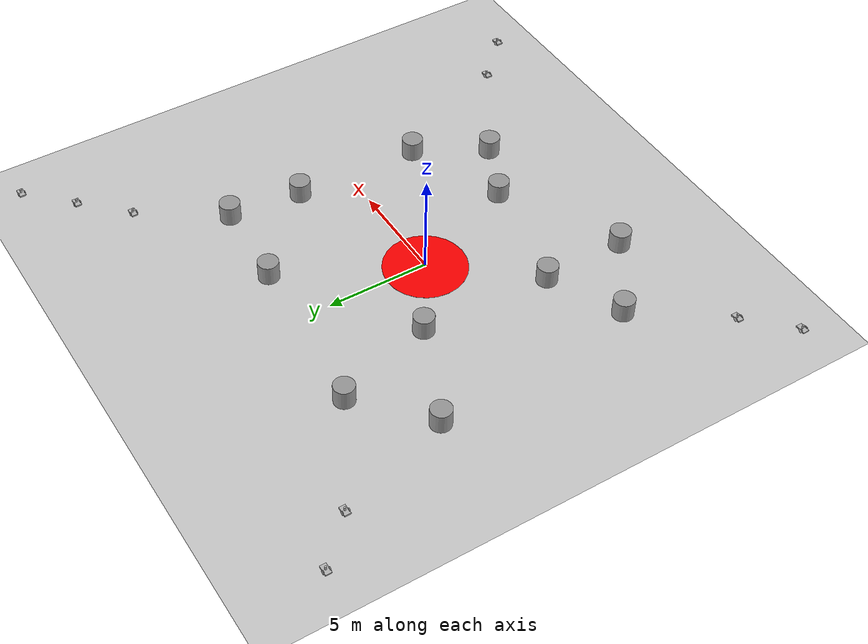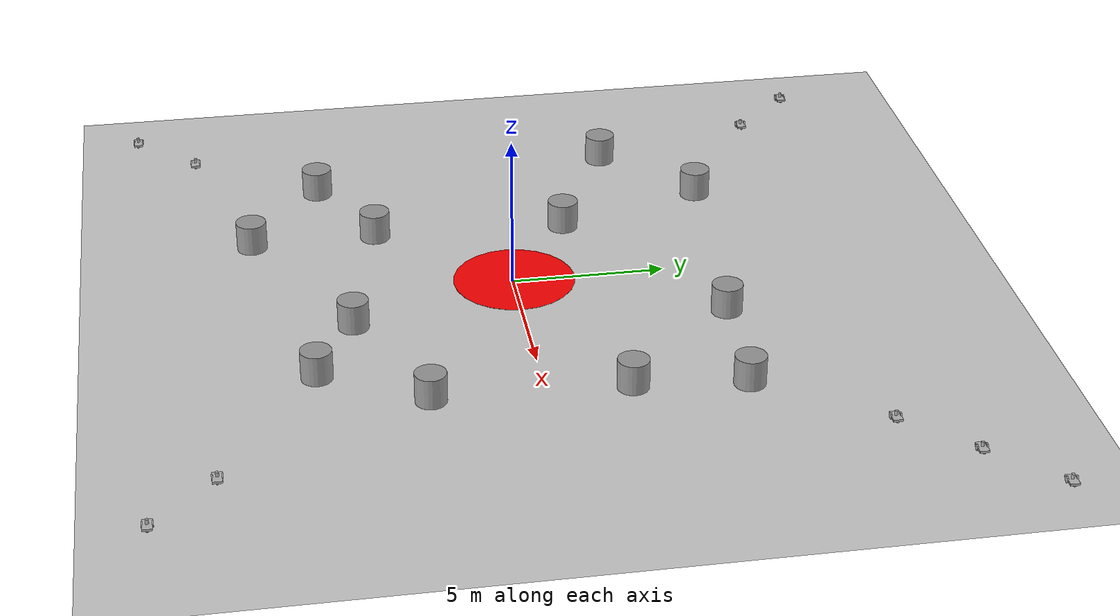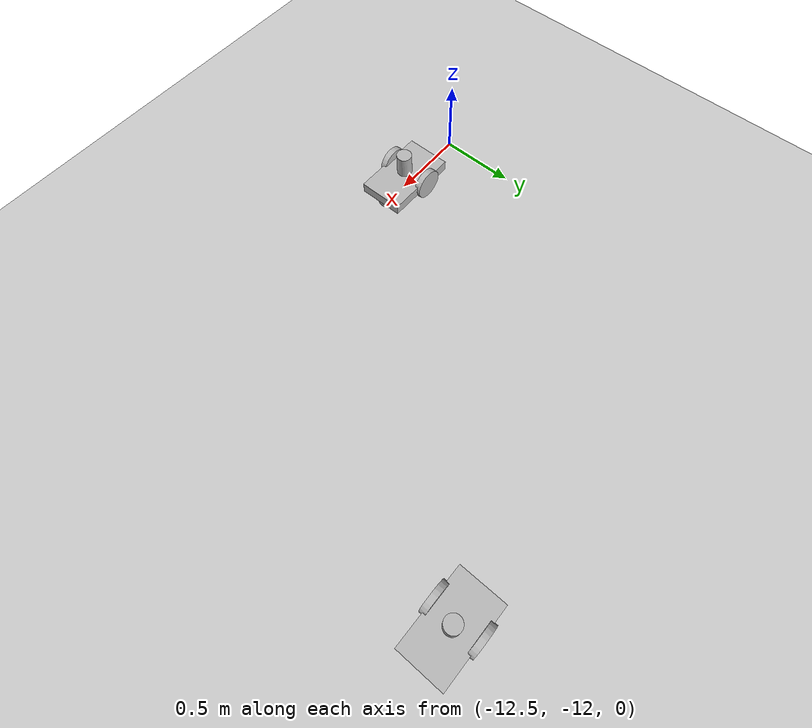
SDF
<sdf version="1.6">
 <world name="default">
  <light name="sun" type="directional">
   <pose>0 0 10 0 -0 0</pose>
   <diffuse>0.8 0.8 0.8 1</diffuse>
   <specular>0.2 0.2 0.2 1</specular>
   <attenuation>
    <range>1000</range>
    <constant>0.9</constant>
    <linear>0.01</linear>
    <quadratic>0.001</quadratic>
   </attenuation>
   <direction>-0.5 0.1 -0.9</direction>
  </light>
  <model name="ground_plane">
   <static>1</static>
   <link name="link">
    <collision name="collision">
     <geometry><plane><normal>0 0 1</normal><size>100 100</size></plane></geometry>
     <surface>
      <contact><collide_bitmask>65535</collide_bitmask></contact>
      <friction><ode><mu>100</mu><mu2>50</mu2></ode></friction>
     </surface>
    </collision>
    <visual name="visual">
     <cast_shadows>0</cast_shadows>
     <geometry><plane><normal>0 0 1</normal><size>100 100</size></plane></geometry>
     <material>
      <script><uri>file://media/materials/scripts/gazebo.material</uri><name>Gazebo/Grey</name></script>
     </material>
    </visual>
   </link>
  </model>
  <gravity>0 0 -9.8</gravity>
  <magnetic_field>6e-06 2.3e-05 -4.2e-05</magnetic_field>
  <atmosphere type="adiabatic"/>
  <physics name="default_physics" default="0" type="ode">
   <max_step_size>0.001</max_step_size>
   <real_time_factor>1</real_time_factor>
   <real_time_update_rate>1000</real_time_update_rate>
  </physics>
  <scene><ambient>0.4 0.4 0.4 1</ambient><background>0.7 0.7 0.7 1</background><shadows>1</shadows></scene>
  <audio><device>default</device></audio>
  <spherical_coordinates>
   <surface_model>EARTH_WGS84</surface_model>
   <latitude_deg>0</latitude_deg>
   <longitude_deg>0</longitude_deg>
   <elevation>0</elevation>
   <heading_deg>0</heading_deg>
  </spherical_coordinates>
  <model name="unit_cylinder_11">
   <link name="link">
    <inertial>
     <mass>100</mass>
     <inertia><ixx>14.5833</ixx><ixy>0</ixy><ixz>0</ixz><iyy>14.5833</iyy><iyz>0</iyz><izz>12.5</izz></inertia>
    </inertial>
    <visual name="visual">
     <geometry><cylinder><radius>0.5</radius><length>1</length></cylinder></geometry>
     <material>
      <script><name>Gazebo/Grey</name><uri>file://media/materials/scripts/gazebo.material</uri></script>
      <shader type="vertex"><normal_map>__default__</normal_map></shader>
     </material>
    </visual>
    <collision name="collision">
     <geometry><cylinder><radius>0.5</radius><length>1</length></cylinder></geometry>
     <surface>
      <friction>
       <ode><mu>1</mu><mu2>1</mu2><fdir1>0 0 0</fdir1><slip1>0</slip1><slip2>0</slip2></ode>
       <torsional>
        <coefficient>1</coefficient>
        <patch_radius>0</patch_radius>
        <surface_radius>0</surface_radius>
        <use_patch_radius>1</use_patch_radius>
        <ode><slip>0</slip></ode>
       </torsional>
      </friction>
      <bounce><restitution_coefficient>0</restitution_coefficient><threshold>1e+06</threshold></bounce>
      <contact>
       <collide_without_contact>0</collide_without_contact>
       <collide_without_contact_bitmask>1</collide_without_contact_bitmask>
       <collide_bitmask>1</collide_bitmask>
       <ode>
        <soft_cfm>0</soft_cfm>
        <soft_erp>0.2</soft_erp>
        <kp>1e+13</kp>
        <kd>1</kd>
        <max_vel>0.01</max_vel>
        <min_depth>0</min_depth>
       </ode>
       <bullet>
        <split_impulse>1</split_impulse>
        <split_impulse_penetration_threshold>-0.01</split_impulse_penetration_threshold>
        <soft_cfm>0</soft_cfm>
        <soft_erp>0.2</soft_erp>
        <kp>1e+13</kp>
        <kd>1</kd>
       </bullet>
      </contact>
     </surface>
    </collision>
   </link>
   <static>0</static>
   <pose>6.79551 -3.49392 0.5 0 -0 0</pose>
  </model>
  <model name="unit_cylinder_11_clone">
   <link name="link">
    <inertial>
     <mass>100</mass>
     <inertia><ixx>14.5833</ixx><ixy>0</ixy><ixz>0</ixz><iyy>14.5833</iyy><iyz>0</iyz><izz>12.5</izz></inertia>
    </inertial>
    <visual name="visual">
     <geometry><cylinder><radius>0.5</radius><length>1</length></cylinder></geometry>
     <material>
      <script><name>Gazebo/Grey</name><uri>file://media/materials/scripts/gazebo.material</uri></script>
      <shader type="vertex"><normal_map>__default__</normal_map></shader>
     </material>
    </visual>
    <collision name="collision">
     <geometry><cylinder><radius>0.5</radius><length>1</length></cylinder></geometry>
     <surface>
      <friction>
       <ode><mu>1</mu><mu2>1</mu2><fdir1>0 0 0</fdir1><slip1>0</slip1><slip2>0</slip2></ode>
       <torsional>
        <coefficient>1</coefficient>
        <patch_radius>0</patch_radius>
        <surface_radius>0</surface_radius>
        <use_patch_radius>1</use_patch_radius>
        <ode><slip>0</slip></ode>
       </torsional>
      </friction>
      <bounce><restitution_coefficient>0</restitution_coefficient><threshold>1e+06</threshold></bounce>
      <contact>
       <collide_without_contact>0</collide_without_contact>
       <collide_without_contact_bitmask>1</collide_without_contact_bitmask>
       <collide_bitmask>1</collide_bitmask>
       <ode>
        <soft_cfm>0</soft_cfm>
        <soft_erp>0.2</soft_erp>
        <kp>1e+13</kp>
        <kd>1</kd>
        <max_vel>0.01</max_vel>
        <min_depth>0</min_depth>
       </ode>
       <bullet>
        <split_impulse>1</split_impulse>
        <split_impulse_penetration_threshold>-0.01</split_impulse_penetration_threshold>
        <soft_cfm>0</soft_cfm>
        <soft_erp>0.2</soft_erp>
        <kp>1e+13</kp>
        <kd>1</kd>
       </bullet>
      </contact>
     </surface>
    </collision>
   </link>
   <static>0</static>
   <pose>2.1015 -5.40557 0.5 0 -0 0</pose>
  </model>
  <model name="unit_cylinder_11_clone_0">
   <link name="link">
    <inertial>
     <mass>100</mass>
     <inertia><ixx>14.5833</ixx><ixy>0</ixy><ixz>0</ixz><iyy>14.5833</iyy><iyz>0</iyz><izz>12.5</izz></inertia>
    </inertial>
    <visual name="visual">
     <geometry><cylinder><radius>0.5</radius><length>1</length></cylinder></geometry>
     <material>
      <script><name>Gazebo/Grey</name><uri>file://media/materials/scripts/gazebo.material</uri></script>
      <shader type="vertex"><normal_map>__default__</normal_map></shader>
     </material>
    </visual>
    <collision name="collision">
     <geometry><cylinder><radius>0.5</radius><length>1</length></cylinder></geometry>
     <surface>
      <friction>
       <ode><mu>1</mu><mu2>1</mu2><fdir1>0 0 0</fdir1><slip1>0</slip1><slip2>0</slip2></ode>
       <torsional>
        <coefficient>1</coefficient>
        <patch_radius>0</patch_radius>
        <surface_radius>0</surface_radius>
        <use_patch_radius>1</use_patch_radius>
        <ode><slip>0</slip></ode>
       </torsional>
      </friction>
      <bounce><restitution_coefficient>0</restitution_coefficient><threshold>1e+06</threshold></bounce>
      <contact>
       <collide_without_contact>0</collide_without_contact>
       <collide_without_contact_bitmask>1</collide_without_contact_bitmask>
       <collide_bitmask>1</collide_bitmask>
       <ode>
        <soft_cfm>0</soft_cfm>
        <soft_erp>0.2</soft_erp>
        <kp>1e+13</kp>
        <kd>1</kd>
        <max_vel>0.01</max_vel>
        <min_depth>0</min_depth>
       </ode>
       <bullet>
        <split_impulse>1</split_impulse>
        <split_impulse_penetration_threshold>-0.01</split_impulse_penetration_threshold>
        <soft_cfm>0</soft_cfm>
        <soft_erp>0.2</soft_erp>
        <kp>1e+13</kp>
        <kd>1</kd>
       </bullet>
      </contact>
     </surface>
    </collision>
   </link>
   <static>0</static>
   <pose>4.95526 -6.78188 0.5 0 -0 0</pose>
  </model>
  <model name="unit_cylinder_11_clone_1">
   <link name="link">
    <inertial>
     <mass>100</mass>
     <inertia><ixx>14.5833</ixx><ixy>0</ixy><ixz>0</ixz><iyy>14.5833</iyy><iyz>0</iyz><izz>12.5</izz></inertia>
    </inertial>
    <visual name="visual">
     <geometry><cylinder><radius>0.5</radius><length>1</length></cylinder></geometry>
     <material>
      <script><name>Gazebo/Grey</name><uri>file://media/materials/scripts/gazebo.material</uri></script>
      <shader type="vertex"><normal_map>__default__</normal_map></shader>
     </material>
    </visual>
    <collision name="collision">
     <geometry><cylinder><radius>0.5</radius><length>1</length></cylinder></geometry>
     <surface>
      <friction>
       <ode><mu>1</mu><mu2>1</mu2><fdir1>0 0 0</fdir1><slip1>0</slip1><slip2>0</slip2></ode>
       <torsional>
        <coefficient>1</coefficient>
        <patch_radius>0</patch_radius>
        <surface_radius>0</surface_radius>
        <use_patch_radius>1</use_patch_radius>
        <ode><slip>0</slip></ode>
       </torsional>
      </friction>
      <bounce><restitution_coefficient>0</restitution_coefficient><threshold>1e+06</threshold></bounce>
      <contact>
       <collide_without_contact>0</collide_without_contact>
       <collide_without_contact_bitmask>1</collide_without_contact_bitmask>
       <collide_bitmask>1</collide_bitmask>
       <ode>
        <soft_cfm>0</soft_cfm>
        <soft_erp>0.2</soft_erp>
        <kp>1e+13</kp>
        <kd>1</kd>
        <max_vel>0.01</max_vel>
        <min_depth>0</min_depth>
       </ode>
       <bullet>
        <split_impulse>1</split_impulse>
        <split_impulse_penetration_threshold>-0.01</split_impulse_penetration_threshold>
        <soft_cfm>0</soft_cfm>
        <soft_erp>0.2</soft_erp>
        <kp>1e+13</kp>
        <kd>1</kd>
       </bullet>
      </contact>
     </surface>
    </collision>
   </link>
   <static>0</static>
   <pose>-3.59494 -8.3056 0.5 0 -0 0</pose>
  </model>
  <model name="unit_cylinder_11_clone_2">
   <link name="link">
    <inertial>
     <mass>100</mass>
     <inertia><ixx>14.5833</ixx><ixy>0</ixy><ixz>0</ixz><iyy>14.5833</iyy><iyz>0</iyz><izz>12.5</izz></inertia>
    </inertial>
    <visual name="visual">
     <geometry><cylinder><radius>0.5</radius><length>1</length></cylinder></geometry>
     <material>
      <script><name>Gazebo/Grey</name><uri>file://media/materials/scripts/gazebo.material</uri></script>
      <shader type="vertex"><normal_map>__default__</normal_map></shader>
     </material>
    </visual>
    <collision name="collision">
     <geometry><cylinder><radius>0.5</radius><length>1</length></cylinder></geometry>
     <surface>
      <friction>
       <ode><mu>1</mu><mu2>1</mu2><fdir1>0 0 0</fdir1><slip1>0</slip1><slip2>0</slip2></ode>
       <torsional>
        <coefficient>1</coefficient>
        <patch_radius>0</patch_radius>
        <surface_radius>0</surface_radius>
        <use_patch_radius>1</use_patch_radius>
        <ode><slip>0</slip></ode>
       </torsional>
      </friction>
      <bounce><restitution_coefficient>0</restitution_coefficient><threshold>1e+06</threshold></bounce>
      <contact>
       <collide_without_contact>0</collide_without_contact>
       <collide_without_contact_bitmask>1</collide_without_contact_bitmask>
       <collide_bitmask>1</collide_bitmask>
       <ode>
        <soft_cfm>0</soft_cfm>
        <soft_erp>0.2</soft_erp>
        <kp>1e+13</kp>
        <kd>1</kd>
        <max_vel>0.01</max_vel>
        <min_depth>0</min_depth>
       </ode>
       <bullet>
        <split_impulse>1</split_impulse>
        <split_impulse_penetration_threshold>-0.01</split_impulse_penetration_threshold>
        <soft_cfm>0</soft_cfm>
        <soft_erp>0.2</soft_erp>
        <kp>1e+13</kp>
        <kd>1</kd>
       </bullet>
      </contact>
     </surface>
    </collision>
   </link>
   <static>0</static>
   <pose>-7.13423 -5.85046 0.5 0 -0 0</pose>
  </model>
  <model name="unit_cylinder_11_clone_3">
   <link name="link">
    <inertial>
     <mass>100</mass>
     <inertia><ixx>14.5833</ixx><ixy>0</ixy><ixz>0</ixz><iyy>14.5833</iyy><iyz>0</iyz><izz>12.5</izz></inertia>
    </inertial>
    <visual name="visual">
     <geometry><cylinder><radius>0.5</radius><length>1</length></cylinder></geometry>
     <material>
      <script><name>Gazebo/Grey</name><uri>file://media/materials/scripts/gazebo.material</uri></script>
      <shader type="vertex"><normal_map>__default__</normal_map></shader>
     </material>
    </visual>
    <collision name="collision">
     <geometry><cylinder><radius>0.5</radius><length>1</length></cylinder></geometry>
     <surface>
      <friction>
       <ode><mu>1</mu><mu2>1</mu2><fdir1>0 0 0</fdir1><slip1>0</slip1><slip2>0</slip2></ode>
       <torsional>
        <coefficient>1</coefficient>
        <patch_radius>0</patch_radius>
        <surface_radius>0</surface_radius>
        <use_patch_radius>1</use_patch_radius>
        <ode><slip>0</slip></ode>
       </torsional>
      </friction>
      <bounce><restitution_coefficient>0</restitution_coefficient><threshold>1e+06</threshold></bounce>
      <contact>
       <collide_without_contact>0</collide_without_contact>
       <collide_without_contact_bitmask>1</collide_without_contact_bitmask>
       <collide_bitmask>1</collide_bitmask>
       <ode>
        <soft_cfm>0</soft_cfm>
        <soft_erp>0.2</soft_erp>
        <kp>1e+13</kp>
        <kd>1</kd>
        <max_vel>0.01</max_vel>
        <min_depth>0</min_depth>
       </ode>
       <bullet>
        <split_impulse>1</split_impulse>
        <split_impulse_penetration_threshold>-0.01</split_impulse_penetration_threshold>
        <soft_cfm>0</soft_cfm>
        <soft_erp>0.2</soft_erp>
        <kp>1e+13</kp>
        <kd>1</kd>
       </bullet>
      </contact>
     </surface>
    </collision>
   </link>
   <static>0</static>
   <pose>-3.68844 -4.16699 0.5 0 -0 0</pose>
  </model>
  <model name="unit_cylinder_11_clone_4">
   <link name="link">
    <inertial>
     <mass>100</mass>
     <inertia><ixx>14.5833</ixx><ixy>0</ixy><ixz>0</ixz><iyy>14.5833</iyy><iyz>0</iyz><izz>12.5</izz></inertia>
    </inertial>
    <visual name="visual">
     <geometry><cylinder><radius>0.5</radius><length>1</length></cylinder></geometry>
     <material>
      <script><name>Gazebo/Grey</name><uri>file://media/materials/scripts/gazebo.material</uri></script>
      <shader type="vertex"><normal_map>__default__</normal_map></shader>
     </material>
    </visual>
    <collision name="collision">
     <geometry><cylinder><radius>0.5</radius><length>1</length></cylinder></geometry>
     <surface>
      <friction>
       <ode><mu>1</mu><mu2>1</mu2><fdir1>0 0 0</fdir1><slip1>0</slip1><slip2>0</slip2></ode>
       <torsional>
        <coefficient>1</coefficient>
        <patch_radius>0</patch_radius>
        <surface_radius>0</surface_radius>
        <use_patch_radius>1</use_patch_radius>
        <ode><slip>0</slip></ode>
       </torsional>
      </friction>
      <bounce><restitution_coefficient>0</restitution_coefficient><threshold>1e+06</threshold></bounce>
      <contact>
       <collide_without_contact>0</collide_without_contact>
       <collide_without_contact_bitmask>1</collide_without_contact_bitmask>
       <collide_bitmask>1</collide_bitmask>
       <ode>
        <soft_cfm>0</soft_cfm>
        <soft_erp>0.2</soft_erp>
        <kp>1e+13</kp>
        <kd>1</kd>
        <max_vel>0.01</max_vel>
        <min_depth>0</min_depth>
       </ode>
       <bullet>
        <split_impulse>1</split_impulse>
        <split_impulse_penetration_threshold>-0.01</split_impulse_penetration_threshold>
        <soft_cfm>0</soft_cfm>
        <soft_erp>0.2</soft_erp>
        <kp>1e+13</kp>
        <kd>1</kd>
       </bullet>
      </contact>
     </surface>
    </collision>
   </link>
   <static>0</static>
   <pose>-8.20919 4.36885 0.5 0 -0 0</pose>
  </model>
  <model name="unit_cylinder_11_clone_5">
   <link name="link">
    <inertial>
     <mass>100</mass>
     <inertia><ixx>14.5833</ixx><ixy>0</ixy><ixz>0</ixz><iyy>14.5833</iyy><iyz>0</iyz><izz>12.5</izz></inertia>
    </inertial>
    <visual name="visual">
     <geometry><cylinder><radius>0.5</radius><length>1</length></cylinder></geometry>
     <material>
      <script><name>Gazebo/Grey</name><uri>file://media/materials/scripts/gazebo.material</uri></script>
      <shader type="vertex"><normal_map>__default__</normal_map></shader>
     </material>
    </visual>
    <collision name="collision">
     <geometry><cylinder><radius>0.5</radius><length>1</length></cylinder></geometry>
     <surface>
      <friction>
       <ode><mu>1</mu><mu2>1</mu2><fdir1>0 0 0</fdir1><slip1>0</slip1><slip2>0</slip2></ode>
       <torsional>
        <coefficient>1</coefficient>
        <patch_radius>0</patch_radius>
        <surface_radius>0</surface_radius>
        <use_patch_radius>1</use_patch_radius>
        <ode><slip>0</slip></ode>
       </torsional>
      </friction>
      <bounce><restitution_coefficient>0</restitution_coefficient><threshold>1e+06</threshold></bounce>
      <contact>
       <collide_without_contact>0</collide_without_contact>
       <collide_without_contact_bitmask>1</collide_without_contact_bitmask>
       <collide_bitmask>1</collide_bitmask>
       <ode>
        <soft_cfm>0</soft_cfm>
        <soft_erp>0.2</soft_erp>
        <kp>1e+13</kp>
        <kd>1</kd>
        <max_vel>0.01</max_vel>
        <min_depth>0</min_depth>
       </ode>
       <bullet>
        <split_impulse>1</split_impulse>
        <split_impulse_penetration_threshold>-0.01</split_impulse_penetration_threshold>
        <soft_cfm>0</soft_cfm>
        <soft_erp>0.2</soft_erp>
        <kp>1e+13</kp>
        <kd>1</kd>
       </bullet>
      </contact>
     </surface>
    </collision>
   </link>
   <static>0</static>
   <pose>-5.04068 7.16468 0.5 0 -0 0</pose>
  </model>
  <model name="unit_cylinder_11_clone_6">
   <link name="link">
    <inertial>
     <mass>100</mass>
     <inertia><ixx>14.5833</ixx><ixy>0</ixy><ixz>0</ixz><iyy>14.5833</iyy><iyz>0</iyz><izz>12.5</izz></inertia>
    </inertial>
    <visual name="visual">
     <geometry><cylinder><radius>0.5</radius><length>1</length></cylinder></geometry>
     <material>
      <script><name>Gazebo/Grey</name><uri>file://media/materials/scripts/gazebo.material</uri></script>
      <shader type="vertex"><normal_map>__default__</normal_map></shader>
     </material>
    </visual>
    <collision name="collision">
     <geometry><cylinder><radius>0.5</radius><length>1</length></cylinder></geometry>
     <surface>
      <friction>
       <ode><mu>1</mu><mu2>1</mu2><fdir1>0 0 0</fdir1><slip1>0</slip1><slip2>0</slip2></ode>
       <torsional>
        <coefficient>1</coefficient>
        <patch_radius>0</patch_radius>
        <surface_radius>0</surface_radius>
        <use_patch_radius>1</use_patch_radius>
        <ode><slip>0</slip></ode>
       </torsional>
      </friction>
      <bounce><restitution_coefficient>0</restitution_coefficient><threshold>1e+06</threshold></bounce>
      <contact>
       <collide_without_contact>0</collide_without_contact>
       <collide_without_contact_bitmask>1</collide_without_contact_bitmask>
       <collide_bitmask>1</collide_bitmask>
       <ode>
        <soft_cfm>0</soft_cfm>
        <soft_erp>0.2</soft_erp>
        <kp>1e+13</kp>
        <kd>1</kd>
        <max_vel>0.01</max_vel>
        <min_depth>0</min_depth>
       </ode>
       <bullet>
        <split_impulse>1</split_impulse>
        <split_impulse_penetration_threshold>-0.01</split_impulse_penetration_threshold>
        <soft_cfm>0</soft_cfm>
        <soft_erp>0.2</soft_erp>
        <kp>1e+13</kp>
        <kd>1</kd>
       </bullet>
      </contact>
     </surface>
    </collision>
   </link>
   <static>0</static>
   <pose>-3.43309 2.22785 0.5 0 -0 0</pose>
  </model>
  <model name="unit_cylinder_11_clone_7">
   <link name="link">
    <inertial>
     <mass>100</mass>
     <inertia><ixx>14.5833</ixx><ixy>0</ixy><ixz>0</ixz><iyy>14.5833</iyy><iyz>0</iyz><izz>12.5</izz></inertia>
    </inertial>
    <visual name="visual">
     <geometry><cylinder><radius>0.5</radius><length>1</length></cylinder></geometry>
     <material>
      <script><name>Gazebo/Grey</name><uri>file://media/materials/scripts/gazebo.material</uri></script>
      <shader type="vertex"><normal_map>__default__</normal_map></shader>
     </material>
    </visual>
    <collision name="collision">
     <geometry><cylinder><radius>0.5</radius><length>1</length></cylinder></geometry>
     <surface>
      <friction>
       <ode><mu>1</mu><mu2>1</mu2><fdir1>0 0 0</fdir1><slip1>0</slip1><slip2>0</slip2></ode>
       <torsional>
        <coefficient>1</coefficient>
        <patch_radius>0</patch_radius>
        <surface_radius>0</surface_radius>
        <use_patch_radius>1</use_patch_radius>
        <ode><slip>0</slip></ode>
       </torsional>
      </friction>
      <bounce><restitution_coefficient>0</restitution_coefficient><threshold>1e+06</threshold></bounce>
      <contact>
       <collide_without_contact>0</collide_without_contact>
       <collide_without_contact_bitmask>1</collide_without_contact_bitmask>
       <collide_bitmask>1</collide_bitmask>
       <ode>
        <soft_cfm>0</soft_cfm>
        <soft_erp>0.2</soft_erp>
        <kp>1e+13</kp>
        <kd>1</kd>
        <max_vel>0.01</max_vel>
        <min_depth>0</min_depth>
       </ode>
       <bullet>
        <split_impulse>1</split_impulse>
        <split_impulse_penetration_threshold>-0.01</split_impulse_penetration_threshold>
        <soft_cfm>0</soft_cfm>
        <soft_erp>0.2</soft_erp>
        <kp>1e+13</kp>
        <kd>1</kd>
       </bullet>
      </contact>
     </surface>
    </collision>
   </link>
   <static>0</static>
   <pose>3.01056 6.47081 0.5 0 -0 0</pose>
  </model>
  <model name="unit_cylinder_11_clone_8">
   <link name="link">
    <inertial>
     <mass>100</mass>
     <inertia><ixx>14.5833</ixx><ixy>0</ixy><ixz>0</ixz><iyy>14.5833</iyy><iyz>0</iyz><izz>12.5</izz></inertia>
    </inertial>
    <visual name="visual">
     <geometry><cylinder><radius>0.5</radius><length>1</length></cylinder></geometry>
     <material>
      <script><name>Gazebo/Grey</name><uri>file://media/materials/scripts/gazebo.material</uri></script>
      <shader type="vertex"><normal_map>__default__</normal_map></shader>
     </material>
    </visual>
    <collision name="collision">
     <geometry><cylinder><radius>0.5</radius><length>1</length></cylinder></geometry>
     <surface>
      <friction>
       <ode><mu>1</mu><mu2>1</mu2><fdir1>0 0 0</fdir1><slip1>0</slip1><slip2>0</slip2></ode>
       <torsional>
        <coefficient>1</coefficient>
        <patch_radius>0</patch_radius>
        <surface_radius>0</surface_radius>
        <use_patch_radius>1</use_patch_radius>
        <ode><slip>0</slip></ode>
       </torsional>
      </friction>
      <bounce><restitution_coefficient>0</restitution_coefficient><threshold>1e+06</threshold></bounce>
      <contact>
       <collide_without_contact>0</collide_without_contact>
       <collide_without_contact_bitmask>1</collide_without_contact_bitmask>
       <collide_bitmask>1</collide_bitmask>
       <ode>
        <soft_cfm>0</soft_cfm>
        <soft_erp>0.2</soft_erp>
        <kp>1e+13</kp>
        <kd>1</kd>
        <max_vel>0.01</max_vel>
        <min_depth>0</min_depth>
       </ode>
       <bullet>
        <split_impulse>1</split_impulse>
        <split_impulse_penetration_threshold>-0.01</split_impulse_penetration_threshold>
        <soft_cfm>0</soft_cfm>
        <soft_erp>0.2</soft_erp>
        <kp>1e+13</kp>
        <kd>1</kd>
       </bullet>
      </contact>
     </surface>
    </collision>
   </link>
   <static>0</static>
   <pose>6.99797 2.65 0.5 0 -0 0</pose>
  </model>
  <model name="unit_cylinder_11_clone_9">
   <link name="link">
    <inertial>
     <mass>100</mass>
     <inertia><ixx>14.5833</ixx><ixy>0</ixy><ixz>0</ixz><iyy>14.5833</iyy><iyz>0</iyz><izz>12.5</izz></inertia>
    </inertial>
    <visual name="visual">
     <geometry><cylinder><radius>0.5</radius><length>1</length></cylinder></geometry>
     <material>
      <script><name>Gazebo/Grey</name><uri>file://media/materials/scripts/gazebo.material</uri></script>
      <shader type="vertex"><normal_map>__default__</normal_map></shader>
     </material>
    </visual>
    <collision name="collision">
     <geometry><cylinder><radius>0.5</radius><length>1</length></cylinder></geometry>
     <surface>
      <friction>
       <ode><mu>1</mu><mu2>1</mu2><fdir1>0 0 0</fdir1><slip1>0</slip1><slip2>0</slip2></ode>
       <torsional>
        <coefficient>1</coefficient>
        <patch_radius>0</patch_radius>
        <surface_radius>0</surface_radius>
        <use_patch_radius>1</use_patch_radius>
        <ode><slip>0</slip></ode>
       </torsional>
      </friction>
      <bounce><restitution_coefficient>0</restitution_coefficient><threshold>1e+06</threshold></bounce>
      <contact>
       <collide_without_contact>0</collide_without_contact>
       <collide_without_contact_bitmask>1</collide_without_contact_bitmask>
       <collide_bitmask>1</collide_bitmask>
       <ode>
        <soft_cfm>0</soft_cfm>
        <soft_erp>0.2</soft_erp>
        <kp>1e+13</kp>
        <kd>1</kd>
        <max_vel>0.01</max_vel>
        <min_depth>0</min_depth>
       </ode>
       <bullet>
        <split_impulse>1</split_impulse>
        <split_impulse_penetration_threshold>-0.01</split_impulse_penetration_threshold>
        <soft_cfm>0</soft_cfm>
        <soft_erp>0.2</soft_erp>
        <kp>1e+13</kp>
        <kd>1</kd>
       </bullet>
      </contact>
     </surface>
    </collision>
   </link>
   <static>0</static>
   <pose>7.35163 6.19382 0.5 0 -0 0</pose>
  </model>
  <model name="robot_3">
   <link name="robot/link_chassis">
    <inertial>
     <pose>0 0 0.021667 0 -0 0</pose>
     <mass>6</mass>
     <inertia>
      <ixx>0.0931667</ixx>
      <ixy>0</ixy>
      <ixz>0</ixz>
      <iyy>0.2265</iyy>
      <iyz>0</iyz>
      <izz>0.212417</izz>
     </inertia>
    </inertial>
    <collision name="robot/link_chassis_fixed_joint_lump__robot/collision_chassis_collision">
     <geometry><box><size>0.5 0.3 0.07</size></box></geometry>
    </collision>
    <collision name="robot/link_chassis_fixed_joint_lump__robot/caster_front_collision_collision_1">
     <pose>0.35 0 -0.05 0 -0 0</pose>
     <geometry><sphere><radius>0.05</radius></sphere></geometry>
    </collision>
    <collision name="robot/link_chassis_fixed_joint_lump__robot/sensor_laser_collision_2">
     <pose>0 0 0.13 0 -0 0</pose>
     <geometry><cylinder><length>0.15</length><radius>0.05</radius></cylinder></geometry>
    </collision>
    <visual name="robot/link_chassis_visual"><geometry><box><size>0.5 0.3 0.07</size></box></geometry></visual>
    <visual name="robot/link_chassis_fixed_joint_lump__robot/caster_front_visual_visual_1">
     <pose>0.2 0 -0.05 0 -0 0</pose>
     <geometry><sphere><radius>0.05</radius></sphere></geometry>
    </visual>
    <visual name="robot/link_chassis_fixed_joint_lump__robot/sensor_laser_visual_2">
     <pose>0 0 0.13 0 -0 0</pose>
     <geometry><cylinder><length>0.15</length><radius>0.05</radius></cylinder></geometry>
     <material><script><uri>__default__</uri><name>__default__</name></script></material>
    </visual>
    <sensor name="head_hokuyo_sensor" type="ray">
     <visualize>0</visualize>
     <update_rate>20</update_rate>
     <ray>
      <scan>
       <horizontal>
        <samples>720</samples>
        <resolution>1</resolution>
        <min_angle>-1.5707</min_angle>
        <max_angle>1.5707</max_angle>
       </horizontal>
       <vertical><samples>1</samples><min_angle>0</min_angle><max_angle>0</max_angle></vertical>
      </scan>
      <range><min>0.2</min><max>2</max><resolution>0.01</resolution></range>
      <noise><type>gaussian</type><mean>0</mean><stddev>0.01</stddev></noise>
     </ray>
     <plugin name="gazebo_ros_head_hokuyo_controller" filename="libgazebo_ros_laser.so">
      <topicName>laser_scan</topicName>
      <frameName>sensor_laser</frameName>
      <robotNamespace>/robot_3/</robotNamespace>
     </plugin>
     <pose>0 0 0.13 0 -0 0</pose>
    </sensor>
   </link>
   <link name="robot/link_left_wheel">
    <pose>-0.05 -0.15 0 0 -0 0</pose>
    <inertial>
     <pose>0 0 0 -0 1.5707 1.5707</pose>
     <mass>0.2</mass>
     <inertia>
      <ixx>0.000526667</ixx>
      <ixy>0</ixy>
      <ixz>0</ixz>
      <iyy>0.000526667</iyy>
      <iyz>0</iyz>
      <izz>0.001</izz>
     </inertia>
    </inertial>
    <collision name="robot/link_left_wheel_collision_collision">
     <pose>0 0 0 3.14159 1.57079 -1.57089</pose>
     <geometry><cylinder><length>0.04</length><radius>0.1</radius></cylinder></geometry>
    </collision>
    <visual name="robot/link_left_wheel_visual_visual">
     <pose>0 0 0 3.14159 1.57079 -1.57089</pose>
     <geometry><cylinder><length>0.04</length><radius>0.1</radius></cylinder></geometry>
    </visual>
   </link>
   <joint name="robot/joint_left_wheel" type="revolute">
    <child>robot/link_left_wheel</child>
    <parent>robot/link_chassis</parent>
    <axis>
     <xyz>0 1 0</xyz>
     <limit><lower>-1e+16</lower><upper>1e+16</upper></limit>
     <dynamics><spring_reference>0</spring_reference><spring_stiffness>0</spring_stiffness></dynamics>
     <use_parent_model_frame>1</use_parent_model_frame>
    </axis>
   </joint>
   <link name="robot/link_right_wheel">
    <pose>-0.05 0.15 0 0 -0 0</pose>
    <inertial>
     <pose>0 0 0 -0 1.5707 1.5707</pose>
     <mass>0.2</mass>
     <inertia>
      <ixx>0.000526667</ixx>
      <ixy>0</ixy>
      <ixz>0</ixz>
      <iyy>0.000526667</iyy>
      <iyz>0</iyz>
      <izz>0.001</izz>
     </inertia>
    </inertial>
    <collision name="robot/link_right_wheel_collision_collision">
     <pose>0 0 0 3.14159 1.57079 -1.57089</pose>
     <geometry><cylinder><length>0.04</length><radius>0.1</radius></cylinder></geometry>
    </collision>
    <visual name="robot/link_right_wheel_visual_visual">
     <pose>0 0 0 3.14159 1.57079 -1.57089</pose>
     <geometry><cylinder><length>0.04</length><radius>0.1</radius></cylinder></geometry>
    </visual>
   </link>
   <joint name="robot/joint_right_wheel" type="revolute">
    <child>robot/link_right_wheel</child>
    <parent>robot/link_chassis</parent>
    <axis>
     <xyz>0 1 0</xyz>
     <limit><lower>-1e+16</lower><upper>1e+16</upper></limit>
     <dynamics><spring_reference>0</spring_reference><spring_stiffness>0</spring_stiffness></dynamics>
     <use_parent_model_frame>1</use_parent_model_frame>
    </axis>
   </joint>
   <plugin name="gazebo_ros_control" filename="libgazebo_ros_control.so">
    <robotSimType>gazebo_ros_control/DefaultRobotHWSim</robotSimType>
    <legacyModeNS>1</legacyModeNS>
    <robotNamespace>/robot_3/</robotNamespace>
   </plugin>
   <static>0</static>
   <plugin name="differential_drive_controller" filename="libgazebo_ros_diff_drive.so">
    <legacyMode>0</legacyMode>
    <alwaysOn>1</alwaysOn>
    <updateRate>20</updateRate>
    <leftJoint>robot/joint_left_wheel</leftJoint>
    <rightJoint>robot/joint_right_wheel</rightJoint>
    <wheelSeparation>0.2</wheelSeparation>
    <wheelDiameter>0.2</wheelDiameter>
    <torque>0.1</torque>
    <commandTopic>cmd_vel</commandTopic>
    <odometryTopic>odom</odometryTopic>
    <odometryFrame>odom</odometryFrame>
    <robotBaseFrame>link_chassis</robotBaseFrame>
    <robotNamespace>/robot_3/</robotNamespace>
   </plugin>
   <pose>9.99442 10.0023 0.1 0 3e-06 -0.002923</pose>
  </model>
  <model name="robot_9">
   <link name="robot/link_chassis">
    <inertial>
     <pose>0 0 0.021667 0 -0 0</pose>
     <mass>6</mass>
     <inertia>
      <ixx>0.0931667</ixx>
      <ixy>0</ixy>
      <ixz>0</ixz>
      <iyy>0.2265</iyy>
      <iyz>0</iyz>
      <izz>0.212417</izz>
     </inertia>
    </inertial>
    <collision name="robot/link_chassis_fixed_joint_lump__robot/collision_chassis_collision">
     <geometry><box><size>0.5 0.3 0.07</size></box></geometry>
    </collision>
    <collision name="robot/link_chassis_fixed_joint_lump__robot/caster_front_collision_collision_1">
     <pose>0.35 0 -0.05 0 -0 0</pose>
     <geometry><sphere><radius>0.05</radius></sphere></geometry>
    </collision>
    <collision name="robot/link_chassis_fixed_joint_lump__robot/sensor_laser_collision_2">
     <pose>0 0 0.13 0 -0 0</pose>
     <geometry><cylinder><length>0.15</length><radius>0.05</radius></cylinder></geometry>
    </collision>
    <visual name="robot/link_chassis_visual"><geometry><box><size>0.5 0.3 0.07</size></box></geometry></visual>
    <visual name="robot/link_chassis_fixed_joint_lump__robot/caster_front_visual_visual_1">
     <pose>0.2 0 -0.05 0 -0 0</pose>
     <geometry><sphere><radius>0.05</radius></sphere></geometry>
    </visual>
    <visual name="robot/link_chassis_fixed_joint_lump__robot/sensor_laser_visual_2">
     <pose>0 0 0.13 0 -0 0</pose>
     <geometry><cylinder><length>0.15</length><radius>0.05</radius></cylinder></geometry>
     <material><script><uri>__default__</uri><name>__default__</name></script></material>
    </visual>
    <sensor name="head_hokuyo_sensor" type="ray">
     <visualize>0</visualize>
     <update_rate>20</update_rate>
     <ray>
      <scan>
       <horizontal>
        <samples>720</samples>
        <resolution>1</resolution>
        <min_angle>-1.5707</min_angle>
        <max_angle>1.5707</max_angle>
       </horizontal>
       <vertical><samples>1</samples><min_angle>0</min_angle><max_angle>0</max_angle></vertical>
      </scan>
      <range><min>0.2</min><max>2</max><resolution>0.01</resolution></range>
      <noise><type>gaussian</type><mean>0</mean><stddev>0.01</stddev></noise>
     </ray>
     <plugin name="gazebo_ros_head_hokuyo_controller" filename="libgazebo_ros_laser.so">
      <topicName>laser_scan</topicName>
      <frameName>sensor_laser</frameName>
      <robotNamespace>/robot_9/</robotNamespace>
     </plugin>
     <pose>0 0 0.13 0 -0 0</pose>
    </sensor>
   </link>
   <link name="robot/link_left_wheel">
    <pose>-0.05 -0.15 0 0 -0 0</pose>
    <inertial>
     <pose>0 0 0 -0 1.5707 1.5707</pose>
     <mass>0.2</mass>
     <inertia>
      <ixx>0.000526667</ixx>
      <ixy>0</ixy>
      <ixz>0</ixz>
      <iyy>0.000526667</iyy>
      <iyz>0</iyz>
      <izz>0.001</izz>
     </inertia>
    </inertial>
    <collision name="robot/link_left_wheel_collision_collision">
     <pose>0 0 0 3.14159 1.57079 -1.57089</pose>
     <geometry><cylinder><length>0.04</length><radius>0.1</radius></cylinder></geometry>
    </collision>
    <visual name="robot/link_left_wheel_visual_visual">
     <pose>0 0 0 3.14159 1.57079 -1.57089</pose>
     <geometry><cylinder><length>0.04</length><radius>0.1</radius></cylinder></geometry>
    </visual>
   </link>
   <joint name="robot/joint_left_wheel" type="revolute">
    <child>robot/link_left_wheel</child>
    <parent>robot/link_chassis</parent>
    <axis>
     <xyz>0 1 0</xyz>
     <limit><lower>-1e+16</lower><upper>1e+16</upper></limit>
     <dynamics><spring_reference>0</spring_reference><spring_stiffness>0</spring_stiffness></dynamics>
     <use_parent_model_frame>1</use_parent_model_frame>
    </axis>
   </joint>
   <link name="robot/link_right_wheel">
    <pose>-0.05 0.15 0 0 -0 0</pose>
    <inertial>
     <pose>0 0 0 -0 1.5707 1.5707</pose>
     <mass>0.2</mass>
     <inertia>
      <ixx>0.000526667</ixx>
      <ixy>0</ixy>
      <ixz>0</ixz>
      <iyy>0.000526667</iyy>
      <iyz>0</iyz>
      <izz>0.001</izz>
     </inertia>
    </inertial>
    <collision name="robot/link_right_wheel_collision_collision">
     <pose>0 0 0 3.14159 1.57079 -1.57089</pose>
     <geometry><cylinder><length>0.04</length><radius>0.1</radius></cylinder></geometry>
    </collision>
    <visual name="robot/link_right_wheel_visual_visual">
     <pose>0 0 0 3.14159 1.57079 -1.57089</pose>
     <geometry><cylinder><length>0.04</length><radius>0.1</radius></cylinder></geometry>
    </visual>
   </link>
   <joint name="robot/joint_right_wheel" type="revolute">
    <child>robot/link_right_wheel</child>
    <parent>robot/link_chassis</parent>
    <axis>
     <xyz>0 1 0</xyz>
     <limit><lower>-1e+16</lower><upper>1e+16</upper></limit>
     <dynamics><spring_reference>0</spring_reference><spring_stiffness>0</spring_stiffness></dynamics>
     <use_parent_model_frame>1</use_parent_model_frame>
    </axis>
   </joint>
   <plugin name="gazebo_ros_control" filename="libgazebo_ros_control.so">
    <robotSimType>gazebo_ros_control/DefaultRobotHWSim</robotSimType>
    <legacyModeNS>1</legacyModeNS>
    <robotNamespace>/robot_9/</robotNamespace>
   </plugin>
   <static>0</static>
   <plugin name="differential_drive_controller" filename="libgazebo_ros_diff_drive.so">
    <legacyMode>0</legacyMode>
    <alwaysOn>1</alwaysOn>
    <updateRate>20</updateRate>
    <leftJoint>robot/joint_left_wheel</leftJoint>
    <rightJoint>robot/joint_right_wheel</rightJoint>
    <wheelSeparation>0.2</wheelSeparation>
    <wheelDiameter>0.2</wheelDiameter>
    <torque>0.1</torque>
    <commandTopic>cmd_vel</commandTopic>
    <odometryTopic>odom</odometryTopic>
    <odometryFrame>odom</odometryFrame>
    <robotBaseFrame>link_chassis</robotBaseFrame>
    <robotNamespace>/robot_9/</robotNamespace>
   </plugin>
   <pose>13.9945 14.0023 0.099999 0 6e-06 -0.00293</pose>
  </model>
  <model name="robot_6">
   <link name="robot/link_chassis">
    <inertial>
     <pose>0 0 0.021667 0 -0 0</pose>
     <mass>6</mass>
     <inertia>
      <ixx>0.0931667</ixx>
      <ixy>0</ixy>
      <ixz>0</ixz>
      <iyy>0.2265</iyy>
      <iyz>0</iyz>
      <izz>0.212417</izz>
     </inertia>
    </inertial>
    <collision name="robot/link_chassis_fixed_joint_lump__robot/collision_chassis_collision">
     <geometry><box><size>0.5 0.3 0.07</size></box></geometry>
    </collision>
    <collision name="robot/link_chassis_fixed_joint_lump__robot/caster_front_collision_collision_1">
     <pose>0.35 0 -0.05 0 -0 0</pose>
     <geometry><sphere><radius>0.05</radius></sphere></geometry>
    </collision>
    <collision name="robot/link_chassis_fixed_joint_lump__robot/sensor_laser_collision_2">
     <pose>0 0 0.13 0 -0 0</pose>
     <geometry><cylinder><length>0.15</length><radius>0.05</radius></cylinder></geometry>
    </collision>
    <visual name="robot/link_chassis_visual"><geometry><box><size>0.5 0.3 0.07</size></box></geometry></visual>
    <visual name="robot/link_chassis_fixed_joint_lump__robot/caster_front_visual_visual_1">
     <pose>0.2 0 -0.05 0 -0 0</pose>
     <geometry><sphere><radius>0.05</radius></sphere></geometry>
    </visual>
    <visual name="robot/link_chassis_fixed_joint_lump__robot/sensor_laser_visual_2">
     <pose>0 0 0.13 0 -0 0</pose>
     <geometry><cylinder><length>0.15</length><radius>0.05</radius></cylinder></geometry>
     <material><script><uri>__default__</uri><name>__default__</name></script></material>
    </visual>
    <sensor name="head_hokuyo_sensor" type="ray">
     <visualize>0</visualize>
     <update_rate>20</update_rate>
     <ray>
      <scan>
       <horizontal>
        <samples>720</samples>
        <resolution>1</resolution>
        <min_angle>-1.5707</min_angle>
        <max_angle>1.5707</max_angle>
       </horizontal>
       <vertical><samples>1</samples><min_angle>0</min_angle><max_angle>0</max_angle></vertical>
      </scan>
      <range><min>0.2</min><max>2</max><resolution>0.01</resolution></range>
      <noise><type>gaussian</type><mean>0</mean><stddev>0.01</stddev></noise>
     </ray>
     <plugin name="gazebo_ros_head_hokuyo_controller" filename="libgazebo_ros_laser.so">
      <topicName>laser_scan</topicName>
      <frameName>sensor_laser</frameName>
      <robotNamespace>/robot_6/</robotNamespace>
     </plugin>
     <pose>0 0 0.13 0 -0 0</pose>
    </sensor>
   </link>
   <link name="robot/link_left_wheel">
    <pose>-0.05 -0.15 0 0 -0 0</pose>
    <inertial>
     <pose>0 0 0 -0 1.5707 1.5707</pose>
     <mass>0.2</mass>
     <inertia>
      <ixx>0.000526667</ixx>
      <ixy>0</ixy>
      <ixz>0</ixz>
      <iyy>0.000526667</iyy>
      <iyz>0</iyz>
      <izz>0.001</izz>
     </inertia>
    </inertial>
    <collision name="robot/link_left_wheel_collision_collision">
     <pose>0 0 0 3.14159 1.57079 -1.57089</pose>
     <geometry><cylinder><length>0.04</length><radius>0.1</radius></cylinder></geometry>
    </collision>
    <visual name="robot/link_left_wheel_visual_visual">
     <pose>0 0 0 3.14159 1.57079 -1.57089</pose>
     <geometry><cylinder><length>0.04</length><radius>0.1</radius></cylinder></geometry>
    </visual>
   </link>
   <joint name="robot/joint_left_wheel" type="revolute">
    <child>robot/link_left_wheel</child>
    <parent>robot/link_chassis</parent>
    <axis>
     <xyz>0 1 0</xyz>
     <limit><lower>-1e+16</lower><upper>1e+16</upper></limit>
     <dynamics><spring_reference>0</spring_reference><spring_stiffness>0</spring_stiffness></dynamics>
     <use_parent_model_frame>1</use_parent_model_frame>
    </axis>
   </joint>
   <link name="robot/link_right_wheel">
    <pose>-0.05 0.15 0 0 -0 0</pose>
    <inertial>
     <pose>0 0 0 -0 1.5707 1.5707</pose>
     <mass>0.2</mass>
     <inertia>
      <ixx>0.000526667</ixx>
      <ixy>0</ixy>
      <ixz>0</ixz>
      <iyy>0.000526667</iyy>
      <iyz>0</iyz>
      <izz>0.001</izz>
     </inertia>
    </inertial>
    <collision name="robot/link_right_wheel_collision_collision">
     <pose>0 0 0 3.14159 1.57079 -1.57089</pose>
     <geometry><cylinder><length>0.04</length><radius>0.1</radius></cylinder></geometry>
    </collision>
    <visual name="robot/link_right_wheel_visual_visual">
     <pose>0 0 0 3.14159 1.57079 -1.57089</pose>
     <geometry><cylinder><length>0.04</length><radius>0.1</radius></cylinder></geometry>
    </visual>
   </link>
   <joint name="robot/joint_right_wheel" type="revolute">
    <child>robot/link_right_wheel</child>
    <parent>robot/link_chassis</parent>
    <axis>
     <xyz>0 1 0</xyz>
     <limit><lower>-1e+16</lower><upper>1e+16</upper></limit>
     <dynamics><spring_reference>0</spring_reference><spring_stiffness>0</spring_stiffness></dynamics>
     <use_parent_model_frame>1</use_parent_model_frame>
    </axis>
   </joint>
   <plugin name="gazebo_ros_control" filename="libgazebo_ros_control.so">
    <robotSimType>gazebo_ros_control/DefaultRobotHWSim</robotSimType>
    <legacyModeNS>1</legacyModeNS>
    <robotNamespace>/robot_6/</robotNamespace>
   </plugin>
   <static>0</static>
   <plugin name="differential_drive_controller" filename="libgazebo_ros_diff_drive.so">
    <legacyMode>0</legacyMode>
    <alwaysOn>1</alwaysOn>
    <updateRate>20</updateRate>
    <leftJoint>robot/joint_left_wheel</leftJoint>
    <rightJoint>robot/joint_right_wheel</rightJoint>
    <wheelSeparation>0.2</wheelSeparation>
    <wheelDiameter>0.2</wheelDiameter>
    <torque>0.1</torque>
    <commandTopic>cmd_vel</commandTopic>
    <odometryTopic>odom</odometryTopic>
    <odometryFrame>odom</odometryFrame>
    <robotBaseFrame>link_chassis</robotBaseFrame>
    <robotNamespace>/robot_6/</robotNamespace>
   </plugin>
   <pose>-12.0055 12.0023 0.099999 0 6e-06 -0.002931</pose>
  </model>
  <model name="robot_1">
   <link name="robot/link_chassis">
    <inertial>
     <pose>0 0 0.021667 0 -0 0</pose>
     <mass>6</mass>
     <inertia>
      <ixx>0.0931667</ixx>
      <ixy>0</ixy>
      <ixz>0</ixz>
      <iyy>0.2265</iyy>
      <iyz>0</iyz>
      <izz>0.212417</izz>
     </inertia>
    </inertial>
    <collision name="robot/link_chassis_fixed_joint_lump__robot/collision_chassis_collision">
     <geometry><box><size>0.5 0.3 0.07</size></box></geometry>
    </collision>
    <collision name="robot/link_chassis_fixed_joint_lump__robot/caster_front_collision_collision_1">
     <pose>0.35 0 -0.05 0 -0 0</pose>
     <geometry><sphere><radius>0.05</radius></sphere></geometry>
    </collision>
    <collision name="robot/link_chassis_fixed_joint_lump__robot/sensor_laser_collision_2">
     <pose>0 0 0.13 0 -0 0</pose>
     <geometry><cylinder><length>0.15</length><radius>0.05</radius></cylinder></geometry>
    </collision>
    <visual name="robot/link_chassis_visual"><geometry><box><size>0.5 0.3 0.07</size></box></geometry></visual>
    <visual name="robot/link_chassis_fixed_joint_lump__robot/caster_front_visual_visual_1">
     <pose>0.2 0 -0.05 0 -0 0</pose>
     <geometry><sphere><radius>0.05</radius></sphere></geometry>
    </visual>
    <visual name="robot/link_chassis_fixed_joint_lump__robot/sensor_laser_visual_2">
     <pose>0 0 0.13 0 -0 0</pose>
     <geometry><cylinder><length>0.15</length><radius>0.05</radius></cylinder></geometry>
     <material><script><uri>__default__</uri><name>__default__</name></script></material>
    </visual>
    <sensor name="head_hokuyo_sensor" type="ray">
     <visualize>0</visualize>
     <update_rate>20</update_rate>
     <ray>
      <scan>
       <horizontal>
        <samples>720</samples>
        <resolution>1</resolution>
        <min_angle>-1.5707</min_angle>
        <max_angle>1.5707</max_angle>
       </horizontal>
       <vertical><samples>1</samples><min_angle>0</min_angle><max_angle>0</max_angle></vertical>
      </scan>
      <range><min>0.2</min><max>2</max><resolution>0.01</resolution></range>
      <noise><type>gaussian</type><mean>0</mean><stddev>0.01</stddev></noise>
     </ray>
     <plugin name="gazebo_ros_head_hokuyo_controller" filename="libgazebo_ros_laser.so">
      <topicName>laser_scan</topicName>
      <frameName>sensor_laser</frameName>
      <robotNamespace>/robot_1/</robotNamespace>
     </plugin>
     <pose>0 0 0.13 0 -0 0</pose>
    </sensor>
   </link>
   <link name="robot/link_left_wheel">
    <pose>-0.05 -0.15 0 0 -0 0</pose>
    <inertial>
     <pose>0 0 0 -0 1.5707 1.5707</pose>
     <mass>0.2</mass>
     <inertia>
      <ixx>0.000526667</ixx>
      <ixy>0</ixy>
      <ixz>0</ixz>
      <iyy>0.000526667</iyy>
      <iyz>0</iyz>
      <izz>0.001</izz>
     </inertia>
    </inertial>
    <collision name="robot/link_left_wheel_collision_collision">
     <pose>0 0 0 3.14159 1.57079 -1.57089</pose>
     <geometry><cylinder><length>0.04</length><radius>0.1</radius></cylinder></geometry>
    </collision>
    <visual name="robot/link_left_wheel_visual_visual">
     <pose>0 0 0 3.14159 1.57079 -1.57089</pose>
     <geometry><cylinder><length>0.04</length><radius>0.1</radius></cylinder></geometry>
    </visual>
   </link>
   <joint name="robot/joint_left_wheel" type="revolute">
    <child>robot/link_left_wheel</child>
    <parent>robot/link_chassis</parent>
    <axis>
     <xyz>0 1 0</xyz>
     <limit><lower>-1e+16</lower><upper>1e+16</upper></limit>
     <dynamics><spring_reference>0</spring_reference><spring_stiffness>0</spring_stiffness></dynamics>
     <use_parent_model_frame>1</use_parent_model_frame>
    </axis>
   </joint>
   <link name="robot/link_right_wheel">
    <pose>-0.05 0.15 0 0 -0 0</pose>
    <inertial>
     <pose>0 0 0 -0 1.5707 1.5707</pose>
     <mass>0.2</mass>
     <inertia>
      <ixx>0.000526667</ixx>
      <ixy>0</ixy>
      <ixz>0</ixz>
      <iyy>0.000526667</iyy>
      <iyz>0</iyz>
      <izz>0.001</izz>
     </inertia>
    </inertial>
    <collision name="robot/link_right_wheel_collision_collision">
     <pose>0 0 0 3.14159 1.57079 -1.57089</pose>
     <geometry><cylinder><length>0.04</length><radius>0.1</radius></cylinder></geometry>
    </collision>
    <visual name="robot/link_right_wheel_visual_visual">
     <pose>0 0 0 3.14159 1.57079 -1.57089</pose>
     <geometry><cylinder><length>0.04</length><radius>0.1</radius></cylinder></geometry>
    </visual>
   </link>
   <joint name="robot/joint_right_wheel" type="revolute">
    <child>robot/link_right_wheel</child>
    <parent>robot/link_chassis</parent>
    <axis>
     <xyz>0 1 0</xyz>
     <limit><lower>-1e+16</lower><upper>1e+16</upper></limit>
     <dynamics><spring_reference>0</spring_reference><spring_stiffness>0</spring_stiffness></dynamics>
     <use_parent_model_frame>1</use_parent_model_frame>
    </axis>
   </joint>
   <plugin name="gazebo_ros_control" filename="libgazebo_ros_control.so">
    <robotSimType>gazebo_ros_control/DefaultRobotHWSim</robotSimType>
    <legacyModeNS>1</legacyModeNS>
    <robotNamespace>/robot_1/</robotNamespace>
   </plugin>
   <static>0</static>
   <plugin name="differential_drive_controller" filename="libgazebo_ros_diff_drive.so">
    <legacyMode>0</legacyMode>
    <alwaysOn>1</alwaysOn>
    <updateRate>20</updateRate>
    <leftJoint>robot/joint_left_wheel</leftJoint>
    <rightJoint>robot/joint_right_wheel</rightJoint>
    <wheelSeparation>0.2</wheelSeparation>
    <wheelDiameter>0.2</wheelDiameter>
    <torque>0.1</torque>
    <commandTopic>cmd_vel</commandTopic>
    <odometryTopic>odom</odometryTopic>
    <odometryFrame>odom</odometryFrame>
    <robotBaseFrame>link_chassis</robotBaseFrame>
    <robotNamespace>/robot_1/</robotNamespace>
   </plugin>
   <pose>-10.0054 -9.99772 0.1 0 -0 -0.002931</pose>
  </model>
  <model name="robot_5">
   <link name="robot/link_chassis">
    <inertial>
     <pose>0 0 0.021667 0 -0 0</pose>
     <mass>6</mass>
     <inertia>
      <ixx>0.0931667</ixx>
      <ixy>0</ixy>
      <ixz>0</ixz>
      <iyy>0.2265</iyy>
      <iyz>0</iyz>
      <izz>0.212417</izz>
     </inertia>
    </inertial>
    <collision name="robot/link_chassis_fixed_joint_lump__robot/collision_chassis_collision">
     <geometry><box><size>0.5 0.3 0.07</size></box></geometry>
    </collision>
    <collision name="robot/link_chassis_fixed_joint_lump__robot/caster_front_collision_collision_1">
     <pose>0.35 0 -0.05 0 -0 0</pose>
     <geometry><sphere><radius>0.05</radius></sphere></geometry>
    </collision>
    <collision name="robot/link_chassis_fixed_joint_lump__robot/sensor_laser_collision_2">
     <pose>0 0 0.13 0 -0 0</pose>
     <geometry><cylinder><length>0.15</length><radius>0.05</radius></cylinder></geometry>
    </collision>
    <visual name="robot/link_chassis_visual"><geometry><box><size>0.5 0.3 0.07</size></box></geometry></visual>
    <visual name="robot/link_chassis_fixed_joint_lump__robot/caster_front_visual_visual_1">
     <pose>0.2 0 -0.05 0 -0 0</pose>
     <geometry><sphere><radius>0.05</radius></sphere></geometry>
    </visual>
    <visual name="robot/link_chassis_fixed_joint_lump__robot/sensor_laser_visual_2">
     <pose>0 0 0.13 0 -0 0</pose>
     <geometry><cylinder><length>0.15</length><radius>0.05</radius></cylinder></geometry>
     <material><script><uri>__default__</uri><name>__default__</name></script></material>
    </visual>
    <sensor name="head_hokuyo_sensor" type="ray">
     <visualize>0</visualize>
     <update_rate>20</update_rate>
     <ray>
      <scan>
       <horizontal>
        <samples>720</samples>
        <resolution>1</resolution>
        <min_angle>-1.5707</min_angle>
        <max_angle>1.5707</max_angle>
       </horizontal>
       <vertical><samples>1</samples><min_angle>0</min_angle><max_angle>0</max_angle></vertical>
      </scan>
      <range><min>0.2</min><max>2</max><resolution>0.01</resolution></range>
      <noise><type>gaussian</type><mean>0</mean><stddev>0.01</stddev></noise>
     </ray>
     <plugin name="gazebo_ros_head_hokuyo_controller" filename="libgazebo_ros_laser.so">
      <topicName>laser_scan</topicName>
      <frameName>sensor_laser</frameName>
      <robotNamespace>/robot_5/</robotNamespace>
     </plugin>
     <pose>0 0 0.13 0 -0 0</pose>
    </sensor>
   </link>
   <link name="robot/link_left_wheel">
    <pose>-0.05 -0.15 0 0 -0 0</pose>
    <inertial>
     <pose>0 0 0 -0 1.5707 1.5707</pose>
     <mass>0.2</mass>
     <inertia>
      <ixx>0.000526667</ixx>
      <ixy>0</ixy>
      <ixz>0</ixz>
      <iyy>0.000526667</iyy>
      <iyz>0</iyz>
      <izz>0.001</izz>
     </inertia>
    </inertial>
    <collision name="robot/link_left_wheel_collision_collision">
     <pose>0 0 0 3.14159 1.57079 -1.57089</pose>
     <geometry><cylinder><length>0.04</length><radius>0.1</radius></cylinder></geometry>
    </collision>
    <visual name="robot/link_left_wheel_visual_visual">
     <pose>0 0 0 3.14159 1.57079 -1.57089</pose>
     <geometry><cylinder><length>0.04</length><radius>0.1</radius></cylinder></geometry>
    </visual>
   </link>
   <joint name="robot/joint_left_wheel" type="revolute">
    <child>robot/link_left_wheel</child>
    <parent>robot/link_chassis</parent>
    <axis>
     <xyz>0 1 0</xyz>
     <limit><lower>-1e+16</lower><upper>1e+16</upper></limit>
     <dynamics><spring_reference>0</spring_reference><spring_stiffness>0</spring_stiffness></dynamics>
     <use_parent_model_frame>1</use_parent_model_frame>
    </axis>
   </joint>
   <link name="robot/link_right_wheel">
    <pose>-0.05 0.15 0 0 -0 0</pose>
    <inertial>
     <pose>0 0 0 -0 1.5707 1.5707</pose>
     <mass>0.2</mass>
     <inertia>
      <ixx>0.000526667</ixx>
      <ixy>0</ixy>
      <ixz>0</ixz>
      <iyy>0.000526667</iyy>
      <iyz>0</iyz>
      <izz>0.001</izz>
     </inertia>
    </inertial>
    <collision name="robot/link_right_wheel_collision_collision">
     <pose>0 0 0 3.14159 1.57079 -1.57089</pose>
     <geometry><cylinder><length>0.04</length><radius>0.1</radius></cylinder></geometry>
    </collision>
    <visual name="robot/link_right_wheel_visual_visual">
     <pose>0 0 0 3.14159 1.57079 -1.57089</pose>
     <geometry><cylinder><length>0.04</length><radius>0.1</radius></cylinder></geometry>
    </visual>
   </link>
   <joint name="robot/joint_right_wheel" type="revolute">
    <child>robot/link_right_wheel</child>
    <parent>robot/link_chassis</parent>
    <axis>
     <xyz>0 1 0</xyz>
     <limit><lower>-1e+16</lower><upper>1e+16</upper></limit>
     <dynamics><spring_reference>0</spring_reference><spring_stiffness>0</spring_stiffness></dynamics>
     <use_parent_model_frame>1</use_parent_model_frame>
    </axis>
   </joint>
   <plugin name="gazebo_ros_control" filename="libgazebo_ros_control.so">
    <robotSimType>gazebo_ros_control/DefaultRobotHWSim</robotSimType>
    <legacyModeNS>1</legacyModeNS>
    <robotNamespace>/robot_5/</robotNamespace>
   </plugin>
   <static>0</static>
   <plugin name="differential_drive_controller" filename="libgazebo_ros_diff_drive.so">
    <legacyMode>0</legacyMode>
    <alwaysOn>1</alwaysOn>
    <updateRate>20</updateRate>
    <leftJoint>robot/joint_left_wheel</leftJoint>
    <rightJoint>robot/joint_right_wheel</rightJoint>
    <wheelSeparation>0.2</wheelSeparation>
    <wheelDiameter>0.2</wheelDiameter>
    <torque>0.1</torque>
    <commandTopic>cmd_vel</commandTopic>
    <odometryTopic>odom</odometryTopic>
    <odometryFrame>odom</odometryFrame>
    <robotBaseFrame>link_chassis</robotBaseFrame>
    <robotNamespace>/robot_5/</robotNamespace>
   </plugin>
   <pose>-10.0054 10.0023 0.1 0 3e-06 -0.002932</pose>
  </model>
  <model name="robot_4">
   <link name="robot/link_chassis">
    <inertial>
     <pose>0 0 0.021667 0 -0 0</pose>
     <mass>6</mass>
     <inertia>
      <ixx>0.0931667</ixx>
      <ixy>0</ixy>
      <ixz>0</ixz>
      <iyy>0.2265</iyy>
      <iyz>0</iyz>
      <izz>0.212417</izz>
     </inertia>
    </inertial>
    <collision name="robot/link_chassis_fixed_joint_lump__robot/collision_chassis_collision">
     <geometry><box><size>0.5 0.3 0.07</size></box></geometry>
    </collision>
    <collision name="robot/link_chassis_fixed_joint_lump__robot/caster_front_collision_collision_1">
     <pose>0.35 0 -0.05 0 -0 0</pose>
     <geometry><sphere><radius>0.05</radius></sphere></geometry>
    </collision>
    <collision name="robot/link_chassis_fixed_joint_lump__robot/sensor_laser_collision_2">
     <pose>0 0 0.13 0 -0 0</pose>
     <geometry><cylinder><length>0.15</length><radius>0.05</radius></cylinder></geometry>
    </collision>
    <visual name="robot/link_chassis_visual"><geometry><box><size>0.5 0.3 0.07</size></box></geometry></visual>
    <visual name="robot/link_chassis_fixed_joint_lump__robot/caster_front_visual_visual_1">
     <pose>0.2 0 -0.05 0 -0 0</pose>
     <geometry><sphere><radius>0.05</radius></sphere></geometry>
    </visual>
    <visual name="robot/link_chassis_fixed_joint_lump__robot/sensor_laser_visual_2">
     <pose>0 0 0.13 0 -0 0</pose>
     <geometry><cylinder><length>0.15</length><radius>0.05</radius></cylinder></geometry>
     <material><script><uri>__default__</uri><name>__default__</name></script></material>
    </visual>
    <sensor name="head_hokuyo_sensor" type="ray">
     <visualize>0</visualize>
     <update_rate>20</update_rate>
     <ray>
      <scan>
       <horizontal>
        <samples>720</samples>
        <resolution>1</resolution>
        <min_angle>-1.5707</min_angle>
        <max_angle>1.5707</max_angle>
       </horizontal>
       <vertical><samples>1</samples><min_angle>0</min_angle><max_angle>0</max_angle></vertical>
      </scan>
      <range><min>0.2</min><max>2</max><resolution>0.01</resolution></range>
      <noise><type>gaussian</type><mean>0</mean><stddev>0.01</stddev></noise>
     </ray>
     <plugin name="gazebo_ros_head_hokuyo_controller" filename="libgazebo_ros_laser.so">
      <topicName>laser_scan</topicName>
      <frameName>sensor_laser</frameName>
      <robotNamespace>/robot_4/</robotNamespace>
     </plugin>
     <pose>0 0 0.13 0 -0 0</pose>
    </sensor>
   </link>
   <link name="robot/link_left_wheel">
    <pose>-0.05 -0.15 0 0 -0 0</pose>
    <inertial>
     <pose>0 0 0 -0 1.5707 1.5707</pose>
     <mass>0.2</mass>
     <inertia>
      <ixx>0.000526667</ixx>
      <ixy>0</ixy>
      <ixz>0</ixz>
      <iyy>0.000526667</iyy>
      <iyz>0</iyz>
      <izz>0.001</izz>
     </inertia>
    </inertial>
    <collision name="robot/link_left_wheel_collision_collision">
     <pose>0 0 0 3.14159 1.57079 -1.57089</pose>
     <geometry><cylinder><length>0.04</length><radius>0.1</radius></cylinder></geometry>
    </collision>
    <visual name="robot/link_left_wheel_visual_visual">
     <pose>0 0 0 3.14159 1.57079 -1.57089</pose>
     <geometry><cylinder><length>0.04</length><radius>0.1</radius></cylinder></geometry>
    </visual>
   </link>
   <joint name="robot/joint_left_wheel" type="revolute">
    <child>robot/link_left_wheel</child>
    <parent>robot/link_chassis</parent>
    <axis>
     <xyz>0 1 0</xyz>
     <limit><lower>-1e+16</lower><upper>1e+16</upper></limit>
     <dynamics><spring_reference>0</spring_reference><spring_stiffness>0</spring_stiffness></dynamics>
     <use_parent_model_frame>1</use_parent_model_frame>
    </axis>
   </joint>
   <link name="robot/link_right_wheel">
    <pose>-0.05 0.15 0 0 -0 0</pose>
    <inertial>
     <pose>0 0 0 -0 1.5707 1.5707</pose>
     <mass>0.2</mass>
     <inertia>
      <ixx>0.000526667</ixx>
      <ixy>0</ixy>
      <ixz>0</ixz>
      <iyy>0.000526667</iyy>
      <iyz>0</iyz>
      <izz>0.001</izz>
     </inertia>
    </inertial>
    <collision name="robot/link_right_wheel_collision_collision">
     <pose>0 0 0 3.14159 1.57079 -1.57089</pose>
     <geometry><cylinder><length>0.04</length><radius>0.1</radius></cylinder></geometry>
    </collision>
    <visual name="robot/link_right_wheel_visual_visual">
     <pose>0 0 0 3.14159 1.57079 -1.57089</pose>
     <geometry><cylinder><length>0.04</length><radius>0.1</radius></cylinder></geometry>
    </visual>
   </link>
   <joint name="robot/joint_right_wheel" type="revolute">
    <child>robot/link_right_wheel</child>
    <parent>robot/link_chassis</parent>
    <axis>
     <xyz>0 1 0</xyz>
     <limit><lower>-1e+16</lower><upper>1e+16</upper></limit>
     <dynamics><spring_reference>0</spring_reference><spring_stiffness>0</spring_stiffness></dynamics>
     <use_parent_model_frame>1</use_parent_model_frame>
    </axis>
   </joint>
   <plugin name="gazebo_ros_control" filename="libgazebo_ros_control.so">
    <robotSimType>gazebo_ros_control/DefaultRobotHWSim</robotSimType>
    <legacyModeNS>1</legacyModeNS>
    <robotNamespace>/robot_4/</robotNamespace>
   </plugin>
   <static>0</static>
   <plugin name="differential_drive_controller" filename="libgazebo_ros_diff_drive.so">
    <legacyMode>0</legacyMode>
    <alwaysOn>1</alwaysOn>
    <updateRate>20</updateRate>
    <leftJoint>robot/joint_left_wheel</leftJoint>
    <rightJoint>robot/joint_right_wheel</rightJoint>
    <wheelSeparation>0.2</wheelSeparation>
    <wheelDiameter>0.2</wheelDiameter>
    <torque>0.1</torque>
    <commandTopic>cmd_vel</commandTopic>
    <odometryTopic>odom</odometryTopic>
    <odometryFrame>odom</odometryFrame>
    <robotBaseFrame>link_chassis</robotBaseFrame>
    <robotNamespace>/robot_4/</robotNamespace>
   </plugin>
   <pose>11.9947 12.0023 0.1 0 0 -0.002933</pose>
  </model>
  <model name="robot_8">
   <link name="robot/link_chassis">
    <inertial>
     <pose>0 0 0.021667 0 -0 0</pose>
     <mass>6</mass>
     <inertia>
      <ixx>0.0931667</ixx>
      <ixy>0</ixy>
      <ixz>0</ixz>
      <iyy>0.2265</iyy>
      <iyz>0</iyz>
      <izz>0.212417</izz>
     </inertia>
    </inertial>
    <collision name="robot/link_chassis_fixed_joint_lump__robot/collision_chassis_collision">
     <geometry><box><size>0.5 0.3 0.07</size></box></geometry>
    </collision>
    <collision name="robot/link_chassis_fixed_joint_lump__robot/caster_front_collision_collision_1">
     <pose>0.35 0 -0.05 0 -0 0</pose>
     <geometry><sphere><radius>0.05</radius></sphere></geometry>
    </collision>
    <collision name="robot/link_chassis_fixed_joint_lump__robot/sensor_laser_collision_2">
     <pose>0 0 0.13 0 -0 0</pose>
     <geometry><cylinder><length>0.15</length><radius>0.05</radius></cylinder></geometry>
    </collision>
    <visual name="robot/link_chassis_visual"><geometry><box><size>0.5 0.3 0.07</size></box></geometry></visual>
    <visual name="robot/link_chassis_fixed_joint_lump__robot/caster_front_visual_visual_1">
     <pose>0.2 0 -0.05 0 -0 0</pose>
     <geometry><sphere><radius>0.05</radius></sphere></geometry>
    </visual>
    <visual name="robot/link_chassis_fixed_joint_lump__robot/sensor_laser_visual_2">
     <pose>0 0 0.13 0 -0 0</pose>
     <geometry><cylinder><length>0.15</length><radius>0.05</radius></cylinder></geometry>
     <material><script><uri>__default__</uri><name>__default__</name></script></material>
    </visual>
    <sensor name="head_hokuyo_sensor" type="ray">
     <visualize>0</visualize>
     <update_rate>20</update_rate>
     <ray>
      <scan>
       <horizontal>
        <samples>720</samples>
        <resolution>1</resolution>
        <min_angle>-1.5707</min_angle>
        <max_angle>1.5707</max_angle>
       </horizontal>
       <vertical><samples>1</samples><min_angle>0</min_angle><max_angle>0</max_angle></vertical>
      </scan>
      <range><min>0.2</min><max>2</max><resolution>0.01</resolution></range>
      <noise><type>gaussian</type><mean>0</mean><stddev>0.01</stddev></noise>
     </ray>
     <plugin name="gazebo_ros_head_hokuyo_controller" filename="libgazebo_ros_laser.so">
      <topicName>laser_scan</topicName>
      <frameName>sensor_laser</frameName>
      <robotNamespace>/robot_8/</robotNamespace>
     </plugin>
     <pose>0 0 0.13 0 -0 0</pose>
    </sensor>
   </link>
   <link name="robot/link_left_wheel">
    <pose>-0.05 -0.15 0 0 -0 0</pose>
    <inertial>
     <pose>0 0 0 -0 1.5707 1.5707</pose>
     <mass>0.2</mass>
     <inertia>
      <ixx>0.000526667</ixx>
      <ixy>0</ixy>
      <ixz>0</ixz>
      <iyy>0.000526667</iyy>
      <iyz>0</iyz>
      <izz>0.001</izz>
     </inertia>
    </inertial>
    <collision name="robot/link_left_wheel_collision_collision">
     <pose>0 0 0 3.14159 1.57079 -1.57089</pose>
     <geometry><cylinder><length>0.04</length><radius>0.1</radius></cylinder></geometry>
    </collision>
    <visual name="robot/link_left_wheel_visual_visual">
     <pose>0 0 0 3.14159 1.57079 -1.57089</pose>
     <geometry><cylinder><length>0.04</length><radius>0.1</radius></cylinder></geometry>
    </visual>
   </link>
   <joint name="robot/joint_left_wheel" type="revolute">
    <child>robot/link_left_wheel</child>
    <parent>robot/link_chassis</parent>
    <axis>
     <xyz>0 1 0</xyz>
     <limit><lower>-1e+16</lower><upper>1e+16</upper></limit>
     <dynamics><spring_reference>0</spring_reference><spring_stiffness>0</spring_stiffness></dynamics>
     <use_parent_model_frame>1</use_parent_model_frame>
    </axis>
   </joint>
   <link name="robot/link_right_wheel">
    <pose>-0.05 0.15 0 0 -0 0</pose>
    <inertial>
     <pose>0 0 0 -0 1.5707 1.5707</pose>
     <mass>0.2</mass>
     <inertia>
      <ixx>0.000526667</ixx>
      <ixy>0</ixy>
      <ixz>0</ixz>
      <iyy>0.000526667</iyy>
      <iyz>0</iyz>
      <izz>0.001</izz>
     </inertia>
    </inertial>
    <collision name="robot/link_right_wheel_collision_collision">
     <pose>0 0 0 3.14159 1.57079 -1.57089</pose>
     <geometry><cylinder><length>0.04</length><radius>0.1</radius></cylinder></geometry>
    </collision>
    <visual name="robot/link_right_wheel_visual_visual">
     <pose>0 0 0 3.14159 1.57079 -1.57089</pose>
     <geometry><cylinder><length>0.04</length><radius>0.1</radius></cylinder></geometry>
    </visual>
   </link>
   <joint name="robot/joint_right_wheel" type="revolute">
    <child>robot/link_right_wheel</child>
    <parent>robot/link_chassis</parent>
    <axis>
     <xyz>0 1 0</xyz>
     <limit><lower>-1e+16</lower><upper>1e+16</upper></limit>
     <dynamics><spring_reference>0</spring_reference><spring_stiffness>0</spring_stiffness></dynamics>
     <use_parent_model_frame>1</use_parent_model_frame>
    </axis>
   </joint>
   <plugin name="gazebo_ros_control" filename="libgazebo_ros_control.so">
    <robotSimType>gazebo_ros_control/DefaultRobotHWSim</robotSimType>
    <legacyModeNS>1</legacyModeNS>
    <robotNamespace>/robot_8/</robotNamespace>
   </plugin>
   <static>0</static>
   <plugin name="differential_drive_controller" filename="libgazebo_ros_diff_drive.so">
    <legacyMode>0</legacyMode>
    <alwaysOn>1</alwaysOn>
    <updateRate>20</updateRate>
    <leftJoint>robot/joint_left_wheel</leftJoint>
    <rightJoint>robot/joint_right_wheel</rightJoint>
    <wheelSeparation>0.2</wheelSeparation>
    <wheelDiameter>0.2</wheelDiameter>
    <torque>0.1</torque>
    <commandTopic>cmd_vel</commandTopic>
    <odometryTopic>odom</odometryTopic>
    <odometryFrame>odom</odometryFrame>
    <robotBaseFrame>link_chassis</robotBaseFrame>
    <robotNamespace>/robot_8/</robotNamespace>
   </plugin>
   <pose>11.9947 -11.9977 0.1 0 1e-06 -0.002934</pose>
  </model>
  <model name="robot_7">
   <link name="robot/link_chassis">
    <inertial>
     <pose>0 0 0.021667 0 -0 0</pose>
     <mass>6</mass>
     <inertia>
      <ixx>0.0931667</ixx>
      <ixy>0</ixy>
      <ixz>0</ixz>
      <iyy>0.2265</iyy>
      <iyz>0</iyz>
      <izz>0.212417</izz>
     </inertia>
    </inertial>
    <collision name="robot/link_chassis_fixed_joint_lump__robot/collision_chassis_collision">
     <geometry><box><size>0.5 0.3 0.07</size></box></geometry>
    </collision>
    <collision name="robot/link_chassis_fixed_joint_lump__robot/caster_front_collision_collision_1">
     <pose>0.35 0 -0.05 0 -0 0</pose>
     <geometry><sphere><radius>0.05</radius></sphere></geometry>
    </collision>
    <collision name="robot/link_chassis_fixed_joint_lump__robot/sensor_laser_collision_2">
     <pose>0 0 0.13 0 -0 0</pose>
     <geometry><cylinder><length>0.15</length><radius>0.05</radius></cylinder></geometry>
    </collision>
    <visual name="robot/link_chassis_visual"><geometry><box><size>0.5 0.3 0.07</size></box></geometry></visual>
    <visual name="robot/link_chassis_fixed_joint_lump__robot/caster_front_visual_visual_1">
     <pose>0.2 0 -0.05 0 -0 0</pose>
     <geometry><sphere><radius>0.05</radius></sphere></geometry>
    </visual>
    <visual name="robot/link_chassis_fixed_joint_lump__robot/sensor_laser_visual_2">
     <pose>0 0 0.13 0 -0 0</pose>
     <geometry><cylinder><length>0.15</length><radius>0.05</radius></cylinder></geometry>
     <material><script><uri>__default__</uri><name>__default__</name></script></material>
    </visual>
    <sensor name="head_hokuyo_sensor" type="ray">
     <visualize>0</visualize>
     <update_rate>20</update_rate>
     <ray>
      <scan>
       <horizontal>
        <samples>720</samples>
        <resolution>1</resolution>
        <min_angle>-1.5707</min_angle>
        <max_angle>1.5707</max_angle>
       </horizontal>
       <vertical><samples>1</samples><min_angle>0</min_angle><max_angle>0</max_angle></vertical>
      </scan>
      <range><min>0.2</min><max>2</max><resolution>0.01</resolution></range>
      <noise><type>gaussian</type><mean>0</mean><stddev>0.01</stddev></noise>
     </ray>
     <plugin name="gazebo_ros_head_hokuyo_controller" filename="libgazebo_ros_laser.so">
      <topicName>laser_scan</topicName>
      <frameName>sensor_laser</frameName>
      <robotNamespace>/robot_7/</robotNamespace>
     </plugin>
     <pose>0 0 0.13 0 -0 0</pose>
    </sensor>
   </link>
   <link name="robot/link_left_wheel">
    <pose>-0.05 -0.15 0 0 -0 0</pose>
    <inertial>
     <pose>0 0 0 -0 1.5707 1.5707</pose>
     <mass>0.2</mass>
     <inertia>
      <ixx>0.000526667</ixx>
      <ixy>0</ixy>
      <ixz>0</ixz>
      <iyy>0.000526667</iyy>
      <iyz>0</iyz>
      <izz>0.001</izz>
     </inertia>
    </inertial>
    <collision name="robot/link_left_wheel_collision_collision">
     <pose>0 0 0 3.14159 1.57079 -1.57089</pose>
     <geometry><cylinder><length>0.04</length><radius>0.1</radius></cylinder></geometry>
    </collision>
    <visual name="robot/link_left_wheel_visual_visual">
     <pose>0 0 0 3.14159 1.57079 -1.57089</pose>
     <geometry><cylinder><length>0.04</length><radius>0.1</radius></cylinder></geometry>
    </visual>
   </link>
   <joint name="robot/joint_left_wheel" type="revolute">
    <child>robot/link_left_wheel</child>
    <parent>robot/link_chassis</parent>
    <axis>
     <xyz>0 1 0</xyz>
     <limit><lower>-1e+16</lower><upper>1e+16</upper></limit>
     <dynamics><spring_reference>0</spring_reference><spring_stiffness>0</spring_stiffness></dynamics>
     <use_parent_model_frame>1</use_parent_model_frame>
    </axis>
   </joint>
   <link name="robot/link_right_wheel">
    <pose>-0.05 0.15 0 0 -0 0</pose>
    <inertial>
     <pose>0 0 0 -0 1.5707 1.5707</pose>
     <mass>0.2</mass>
     <inertia>
      <ixx>0.000526667</ixx>
      <ixy>0</ixy>
      <ixz>0</ixz>
      <iyy>0.000526667</iyy>
      <iyz>0</iyz>
      <izz>0.001</izz>
     </inertia>
    </inertial>
    <collision name="robot/link_right_wheel_collision_collision">
     <pose>0 0 0 3.14159 1.57079 -1.57089</pose>
     <geometry><cylinder><length>0.04</length><radius>0.1</radius></cylinder></geometry>
    </collision>
    <visual name="robot/link_right_wheel_visual_visual">
     <pose>0 0 0 3.14159 1.57079 -1.57089</pose>
     <geometry><cylinder><length>0.04</length><radius>0.1</radius></cylinder></geometry>
    </visual>
   </link>
   <joint name="robot/joint_right_wheel" type="revolute">
    <child>robot/link_right_wheel</child>
    <parent>robot/link_chassis</parent>
    <axis>
     <xyz>0 1 0</xyz>
     <limit><lower>-1e+16</lower><upper>1e+16</upper></limit>
     <dynamics><spring_reference>0</spring_reference><spring_stiffness>0</spring_stiffness></dynamics>
     <use_parent_model_frame>1</use_parent_model_frame>
    </axis>
   </joint>
   <plugin name="gazebo_ros_control" filename="libgazebo_ros_control.so">
    <robotSimType>gazebo_ros_control/DefaultRobotHWSim</robotSimType>
    <legacyModeNS>1</legacyModeNS>
    <robotNamespace>/robot_7/</robotNamespace>
   </plugin>
   <static>0</static>
   <plugin name="differential_drive_controller" filename="libgazebo_ros_diff_drive.so">
    <legacyMode>0</legacyMode>
    <alwaysOn>1</alwaysOn>
    <updateRate>20</updateRate>
    <leftJoint>robot/joint_left_wheel</leftJoint>
    <rightJoint>robot/joint_right_wheel</rightJoint>
    <wheelSeparation>0.2</wheelSeparation>
    <wheelDiameter>0.2</wheelDiameter>
    <torque>0.1</torque>
    <commandTopic>cmd_vel</commandTopic>
    <odometryTopic>odom</odometryTopic>
    <odometryFrame>odom</odometryFrame>
    <robotBaseFrame>link_chassis</robotBaseFrame>
    <robotNamespace>/robot_7/</robotNamespace>
   </plugin>
   <pose>9.99478 -9.99772 0.1 -0 1e-06 -0.002935</pose>
  </model>
  <model name="robot_2">
   <link name="robot/link_chassis">
    <inertial>
     <pose>0 0 0.021667 0 -0 0</pose>
     <mass>6</mass>
     <inertia>
      <ixx>0.0931667</ixx>
      <ixy>0</ixy>
      <ixz>0</ixz>
      <iyy>0.2265</iyy>
      <iyz>0</iyz>
      <izz>0.212417</izz>
     </inertia>
    </inertial>
    <collision name="robot/link_chassis_fixed_joint_lump__robot/collision_chassis_collision">
     <geometry><box><size>0.5 0.3 0.07</size></box></geometry>
    </collision>
    <collision name="robot/link_chassis_fixed_joint_lump__robot/caster_front_collision_collision_1">
     <pose>0.35 0 -0.05 0 -0 0</pose>
     <geometry><sphere><radius>0.05</radius></sphere></geometry>
    </collision>
    <collision name="robot/link_chassis_fixed_joint_lump__robot/sensor_laser_collision_2">
     <pose>0 0 0.13 0 -0 0</pose>
     <geometry><cylinder><length>0.15</length><radius>0.05</radius></cylinder></geometry>
    </collision>
    <visual name="robot/link_chassis_visual"><geometry><box><size>0.5 0.3 0.07</size></box></geometry></visual>
    <visual name="robot/link_chassis_fixed_joint_lump__robot/caster_front_visual_visual_1">
     <pose>0.2 0 -0.05 0 -0 0</pose>
     <geometry><sphere><radius>0.05</radius></sphere></geometry>
    </visual>
    <visual name="robot/link_chassis_fixed_joint_lump__robot/sensor_laser_visual_2">
     <pose>0 0 0.13 0 -0 0</pose>
     <geometry><cylinder><length>0.15</length><radius>0.05</radius></cylinder></geometry>
     <material><script><uri>__default__</uri><name>__default__</name></script></material>
    </visual>
    <sensor name="head_hokuyo_sensor" type="ray">
     <visualize>0</visualize>
     <update_rate>20</update_rate>
     <ray>
      <scan>
       <horizontal>
        <samples>720</samples>
        <resolution>1</resolution>
        <min_angle>-1.5707</min_angle>
        <max_angle>1.5707</max_angle>
       </horizontal>
       <vertical><samples>1</samples><min_angle>0</min_angle><max_angle>0</max_angle></vertical>
      </scan>
      <range><min>0.2</min><max>2</max><resolution>0.01</resolution></range>
      <noise><type>gaussian</type><mean>0</mean><stddev>0.01</stddev></noise>
     </ray>
     <plugin name="gazebo_ros_head_hokuyo_controller" filename="libgazebo_ros_laser.so">
      <topicName>laser_scan</topicName>
      <frameName>sensor_laser</frameName>
      <robotNamespace>/robot_2/</robotNamespace>
     </plugin>
     <pose>0 0 0.13 0 -0 0</pose>
    </sensor>
   </link>
   <link name="robot/link_left_wheel">
    <pose>-0.05 -0.15 0 0 -0 0</pose>
    <inertial>
     <pose>0 0 0 -0 1.5707 1.5707</pose>
     <mass>0.2</mass>
     <inertia>
      <ixx>0.000526667</ixx>
      <ixy>0</ixy>
      <ixz>0</ixz>
      <iyy>0.000526667</iyy>
      <iyz>0</iyz>
      <izz>0.001</izz>
     </inertia>
    </inertial>
    <collision name="robot/link_left_wheel_collision_collision">
     <pose>0 0 0 3.14159 1.57079 -1.57089</pose>
     <geometry><cylinder><length>0.04</length><radius>0.1</radius></cylinder></geometry>
    </collision>
    <visual name="robot/link_left_wheel_visual_visual">
     <pose>0 0 0 3.14159 1.57079 -1.57089</pose>
     <geometry><cylinder><length>0.04</length><radius>0.1</radius></cylinder></geometry>
    </visual>
   </link>
   <joint name="robot/joint_left_wheel" type="revolute">
    <child>robot/link_left_wheel</child>
    <parent>robot/link_chassis</parent>
    <axis>
     <xyz>0 1 0</xyz>
     <limit><lower>-1e+16</lower><upper>1e+16</upper></limit>
     <dynamics><spring_reference>0</spring_reference><spring_stiffness>0</spring_stiffness></dynamics>
     <use_parent_model_frame>1</use_parent_model_frame>
    </axis>
   </joint>
   <link name="robot/link_right_wheel">
    <pose>-0.05 0.15 0 0 -0 0</pose>
    <inertial>
     <pose>0 0 0 -0 1.5707 1.5707</pose>
     <mass>0.2</mass>
     <inertia>
      <ixx>0.000526667</ixx>
      <ixy>0</ixy>
      <ixz>0</ixz>
      <iyy>0.000526667</iyy>
      <iyz>0</iyz>
      <izz>0.001</izz>
     </inertia>
    </inertial>
    <collision name="robot/link_right_wheel_collision_collision">
     <pose>0 0 0 3.14159 1.57079 -1.57089</pose>
     <geometry><cylinder><length>0.04</length><radius>0.1</radius></cylinder></geometry>
    </collision>
    <visual name="robot/link_right_wheel_visual_visual">
     <pose>0 0 0 3.14159 1.57079 -1.57089</pose>
     <geometry><cylinder><length>0.04</length><radius>0.1</radius></cylinder></geometry>
    </visual>
   </link>
   <joint name="robot/joint_right_wheel" type="revolute">
    <child>robot/link_right_wheel</child>
    <parent>robot/link_chassis</parent>
    <axis>
     <xyz>0 1 0</xyz>
     <limit><lower>-1e+16</lower><upper>1e+16</upper></limit>
     <dynamics><spring_reference>0</spring_reference><spring_stiffness>0</spring_stiffness></dynamics>
     <use_parent_model_frame>1</use_parent_model_frame>
    </axis>
   </joint>
   <plugin name="gazebo_ros_control" filename="libgazebo_ros_control.so">
    <robotSimType>gazebo_ros_control/DefaultRobotHWSim</robotSimType>
    <legacyModeNS>1</legacyModeNS>
    <robotNamespace>/robot_2/</robotNamespace>
   </plugin>
   <static>0</static>
   <plugin name="differential_drive_controller" filename="libgazebo_ros_diff_drive.so">
    <legacyMode>0</legacyMode>
    <alwaysOn>1</alwaysOn>
    <updateRate>20</updateRate>
    <leftJoint>robot/joint_left_wheel</leftJoint>
    <rightJoint>robot/joint_right_wheel</rightJoint>
    <wheelSeparation>0.2</wheelSeparation>
    <wheelDiameter>0.2</wheelDiameter>
    <torque>0.1</torque>
    <commandTopic>cmd_vel</commandTopic>
    <odometryTopic>odom</odometryTopic>
    <odometryFrame>odom</odometryFrame>
    <robotBaseFrame>link_chassis</robotBaseFrame>
    <robotNamespace>/robot_2/</robotNamespace>
   </plugin>
   <pose>-12.0052 -11.9977 0.1 0 -1e-06 -0.002941</pose>
  </model>
  <model name="target_1">
   <link name="link_0">
    <inertial>
     <mass>1</mass>
     <inertia><ixx>0.145833</ixx><ixy>0</ixy><ixz>0</ixz><iyy>0.145833</iyy><iyz>0</iyz><izz>0.125</izz></inertia>
    </inertial>
    <pose>-0.058186 0.0294 8e-06 3e-06 4e-06 -0</pose>
    <visual name="visual">
     <pose>0 0 -0.49 0 -0 0</pose>
     <geometry><cylinder><radius>2</radius><length>0.005</length></cylinder></geometry>
     <material>
      <lighting>1</lighting>
      <script><uri>file://media/materials/scripts/gazebo.material</uri><name>Gazebo/Grey</name></script>
      <shader type="vertex"><normal_map>__default__</normal_map></shader>
      <ambient>1 0 0 0</ambient>
      <diffuse>0.7 0.7 0.7 1</diffuse>
      <specular>0.01 0.01 0.01 1</specular>
      <emissive>0 0 0 1</emissive>
     </material>
    </visual>
    <collision name="collision">
     <pose>0 0 -0.49 0 -0 0</pose>
     <geometry><cylinder><radius>2</radius><length>0.005</length></cylinder></geometry>
     <surface>
      <friction>
       <ode><mu>1</mu><mu2>1</mu2><fdir1>0 0 0</fdir1><slip1>0</slip1><slip2>0</slip2></ode>
       <torsional>
        <coefficient>1</coefficient>
        <patch_radius>0</patch_radius>
        <surface_radius>0</surface_radius>
        <use_patch_radius>1</use_patch_radius>
        <ode><slip>0</slip></ode>
       </torsional>
      </friction>
      <bounce><restitution_coefficient>0</restitution_coefficient><threshold>1e+06</threshold></bounce>
      <contact>
       <collide_without_contact>0</collide_without_contact>
       <collide_without_contact_bitmask>1</collide_without_contact_bitmask>
       <collide_bitmask>1</collide_bitmask>
       <ode>
        <soft_cfm>0</soft_cfm>
        <soft_erp>0.2</soft_erp>
        <kp>1e+13</kp>
        <kd>1</kd>
        <max_vel>0.01</max_vel>
        <min_depth>0</min_depth>
       </ode>
       <bullet>
        <split_impulse>1</split_impulse>
        <split_impulse_penetration_threshold>-0.01</split_impulse_penetration_threshold>
        <soft_cfm>0</soft_cfm>
        <soft_erp>0.2</soft_erp>
        <kp>1e+13</kp>
        <kd>1</kd>
       </bullet>
      </contact>
     </surface>
    </collision>
   </link>
   <static>0</static>
   <pose>-0.041017 0.031627 0.499993 -3e-06 -4e-06 -0</pose>
  </model>
 </world>
</sdf>
